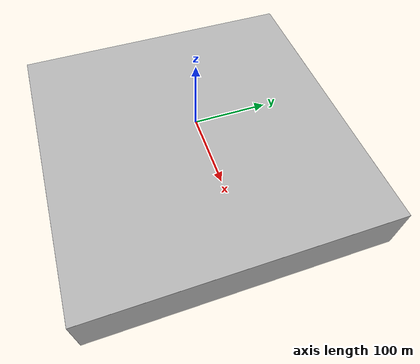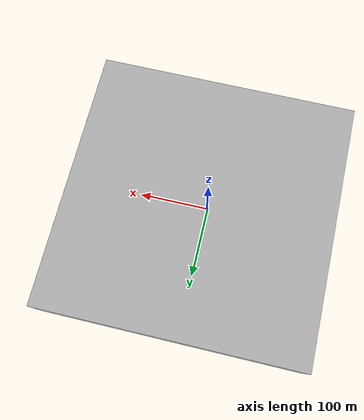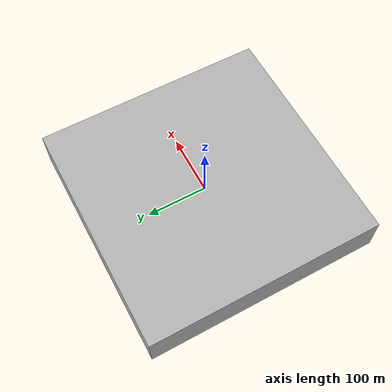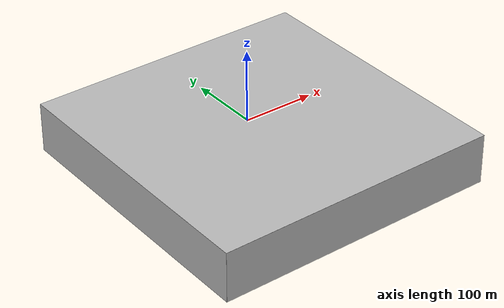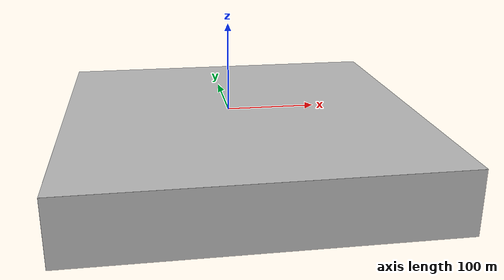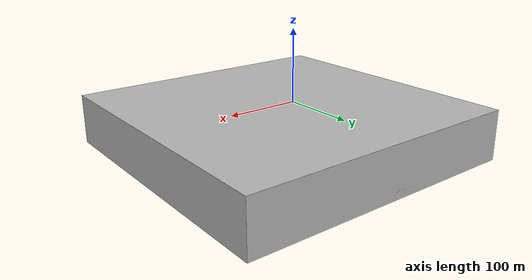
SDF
<sdf version="1.7">
 <world name="munkholmen">
  <physics name="default_physics" default="1" type="ode">
   <max_step_size>0.01</max_step_size>
   <real_time_factor>1</real_time_factor>
   <real_time_update_rate>100</real_time_update_rate>
   <ode>
    <solver>
     <type>quick</type>
     <iters>50</iters>
     <sor>1.2</sor>
     <use_dynamic_moi_rescaling>0</use_dynamic_moi_rescaling>
    </solver>
    <constraints>
     <cfm>0</cfm>
     <erp>0.2</erp>
     <contact_max_correcting_vel>100</contact_max_correcting_vel>
     <contact_surface_layer>0.001</contact_surface_layer>
    </constraints>
   </ode>
  </physics>
  <scene>
   <ambient>0.01 0.01 0.01 1</ambient>
   <sky><clouds><speed>12</speed></clouds></sky>
   <shadows>1</shadows>
   <fog><color>0.1 0.2 0.3 1</color><type>linear</type><density>0.1</density><start>10</start><end>40</end></fog>
   <background>0.7 0.7 0.7 1</background>
  </scene>
  <spherical_coordinates>
   <latitude_deg>63.4534</latitude_deg>
   <longitude_deg>10.4056</longitude_deg>
   <surface_model>EARTH_WGS84</surface_model>
   <elevation>0</elevation>
   <heading_deg>0</heading_deg>
  </spherical_coordinates>
  <light name="sun_diffuse_1" type="directional">
   <pose>-200 -200 100 0 -0 0</pose>
   <diffuse>0.6 0.6 0.6 1</diffuse>
   <specular>0 0 0 1</specular>
   <direction>-0.3 -0.3 -1</direction>
   <attenuation><range>10</range></attenuation>
   <spot><inner_angle>0</inner_angle><outer_angle>0</outer_angle><falloff>0</falloff></spot>
  </light>
  <light name="sun_diffuse_2" type="directional">
   <pose>-100 50 200 0 -0 0</pose>
   <diffuse>0.6 0.6 0.6 1</diffuse>
   <specular>0 0 0 1</specular>
   <direction>-0.3 -0.3 -1</direction>
   <attenuation><range>10</range></attenuation>
   <spot><inner_angle>0</inner_angle><outer_angle>0</outer_angle><falloff>0</falloff></spot>
  </light>
  <light name="sun_diffuse_3" type="directional">
   <pose>-150 -130 50 0 -0 0</pose>
   <diffuse>0.6 0.6 0.6 1</diffuse>
   <specular>0.2 0.2 0.2 1</specular>
   <direction>0.5 0.5 -1</direction>
   <attenuation><range>10</range></attenuation>
   <spot><inner_angle>0</inner_angle><outer_angle>0</outer_angle><falloff>0</falloff></spot>
  </light>
  <model name="herkules_seabed">
   <static>1</static>
   <link name="seabed">
    <collision name="seabed">
     <pose>0 0 -60 0 -0 0</pose>
     <geometry>
      <mesh><uri>model://herkules_seabed/meshes/herkules_seabed.dae</uri><scale>4 4 1</scale></mesh>
     </geometry>
    </collision>
    <visual name="seabed">
     <pose>0 0 -60 0 -0 0</pose>
     <geometry>
      <mesh><uri>model://herkules_seabed/meshes/herkules_seabed.dae</uri><scale>4 4 1</scale></mesh>
     </geometry>
     <material>
      <script>
       <uri>file://Media/materials/scripts/sand.material</uri>
       <name>UUVSimulator/SandAndStones</name>
      </script>
     </material>
    </visual>
   </link>
   <link name="ocean_link">
    <visual name="surface">
     <cast_shadows>0</cast_shadows>
     <geometry><box><size>400 400 0.1</size></box></geometry>
     <material>
      <script><uri>file://Media/materials/scripts/water.material</uri><name>UUVSimulator/StaticWater</name></script>
     </material>
    </visual>
    <visual name="bottom">
     <pose>0 0 -70 0 -0 0</pose>
     <geometry><box><size>400 400 0.1</size></box></geometry>
     <material>
      <script><uri>file://Media/materials/scripts/water.material</uri><name>UUVSimulator/SeaWall</name></script>
     </material>
    </visual>
    <visual name="north_wall">
     <pose>0 200 -35 0 -0 0</pose>
     <geometry><box><size>400 0.1 70</size></box></geometry>
     <material>
      <script><uri>file://Media/materials/scripts/water.material</uri><name>UUVSimulator/SeaWall</name></script>
     </material>
    </visual>
    <visual name="south_wall">
     <pose>0 -200 -35 0 -0 0</pose>
     <geometry><box><size>400 0.1 70</size></box></geometry>
     <material>
      <script><uri>file://Media/materials/scripts/water.material</uri><name>UUVSimulator/SeaWall</name></script>
     </material>
    </visual>
    <visual name="east_wall">
     <pose>200 0 -35 0 -0 0</pose>
     <geometry><box><size>0.1 400 70</size></box></geometry>
     <material>
      <script><uri>file://Media/materials/scripts/water.material</uri><name>UUVSimulator/SeaWall</name></script>
     </material>
    </visual>
    <visual name="west_wall">
     <pose>-200 0 -35 0 -0 0</pose>
     <geometry><box><size>0.1 400 70</size></box></geometry>
     <material>
      <script><uri>file://Media/materials/scripts/water.material</uri><name>UUVSimulator/SeaWall</name></script>
     </material>
    </visual>
   </link>
   <pose>13.2207 -6.8659 0 0 -0 0</pose>
  </model>
  <plugin name="underwater_current_plugin" filename="libuuv_underwater_current_ros_plugin.so">
   <namespace>hydrodynamics</namespace>
   <constant_current>
    <topic>current_velocity</topic>
    <velocity><mean>0</mean><min>0</min><max>5</max><mu>0.0</mu><noiseAmp>0.0</noiseAmp></velocity>
    <horizontal_angle>
     <mean>0</mean>
     <min>-3.141592653589793238</min>
     <max>3.141592653589793238</max>
     <mu>0.0</mu>
     <noiseAmp>0.0</noiseAmp>
    </horizontal_angle>
    <vertical_angle>
     <mean>0</mean>
     <min>-3.141592653589793238</min>
     <max>3.141592653589793238</max>
     <mu>0.0</mu>
     <noiseAmp>0.0</noiseAmp>
    </vertical_angle>
   </constant_current>
  </plugin>
  <plugin name="sc_interface" filename="libuuv_sc_ros_interface_plugin.so"/>
  <gravity>0 0 -9.8</gravity>
  <magnetic_field>6e-06 2.3e-05 -4.2e-05</magnetic_field>
  <atmosphere type="adiabatic"/>
  <model name="person_standing">
   <link name="person_standing::link">
    <inertial>
     <pose>0 -0.1 0.95 0 -0 0</pose>
     <mass>80</mass>
     <inertia><ixx>24.88</ixx><ixy>0</ixy><ixz>0</ixz><iyy>25.73</iyy><iyz>0</iyz><izz>2.48</izz></inertia>
    </inertial>
    <visual name="visual">
     <pose>0 0 0.02 0.04 -0 0</pose>
     <geometry><mesh><uri>model://person_standing/meshes/standing.dae</uri></mesh></geometry>
     <material><shader type="pixel"/></material>
    </visual>
    <collision name="bottom">
     <pose>0 -0.1 0.01 0 -0 0</pose>
     <geometry><box><size>0.5 0.35 0.02</size></box></geometry>
     <surface>
      <friction>
       <ode><mu>1</mu><mu2>1</mu2><fdir1>0 0 0</fdir1><slip1>0</slip1><slip2>0</slip2></ode>
       <torsional>
        <coefficient>1</coefficient>
        <patch_radius>0</patch_radius>
        <surface_radius>0</surface_radius>
        <use_patch_radius>1</use_patch_radius>
        <ode><slip>0</slip></ode>
       </torsional>
      </friction>
      <bounce><restitution_coefficient>0</restitution_coefficient><threshold>1e+06</threshold></bounce>
      <contact>
       <collide_without_contact>0</collide_without_contact>
       <collide_without_contact_bitmask>1</collide_without_contact_bitmask>
       <collide_bitmask>1</collide_bitmask>
       <ode>
        <soft_cfm>0</soft_cfm>
        <soft_erp>0.2</soft_erp>
        <kp>1e+13</kp>
        <kd>1</kd>
        <max_vel>0.01</max_vel>
        <min_depth>0</min_depth>
       </ode>
       <bullet>
        <split_impulse>1</split_impulse>
        <split_impulse_penetration_threshold>-0.01</split_impulse_penetration_threshold>
        <soft_cfm>0</soft_cfm>
        <soft_erp>0.2</soft_erp>
        <kp>1e+13</kp>
        <kd>1</kd>
       </bullet>
      </contact>
     </surface>
    </collision>
    <collision name="person">
     <pose>0 0 0.02 0.04 -0 0</pose>
     <geometry>
      <mesh><uri>/home/vaibhav/.gazebo/models/person_standing/meshes/standing.dae</uri><scale>1 1 1</scale></mesh>
     </geometry>
     <surface>
      <friction>
       <ode><mu>1</mu><mu2>1</mu2><fdir1>0 0 0</fdir1><slip1>0</slip1><slip2>0</slip2></ode>
       <torsional>
        <coefficient>1</coefficient>
        <patch_radius>0</patch_radius>
        <surface_radius>0</surface_radius>
        <use_patch_radius>1</use_patch_radius>
        <ode><slip>0</slip></ode>
       </torsional>
      </friction>
      <bounce><restitution_coefficient>0</restitution_coefficient><threshold>1e+06</threshold></bounce>
      <contact>
       <collide_without_contact>0</collide_without_contact>
       <collide_without_contact_bitmask>1</collide_without_contact_bitmask>
       <collide_bitmask>1</collide_bitmask>
       <ode>
        <soft_cfm>0</soft_cfm>
        <soft_erp>0.2</soft_erp>
        <kp>1e+13</kp>
        <kd>1</kd>
        <max_vel>0.01</max_vel>
        <min_depth>0</min_depth>
       </ode>
       <bullet>
        <split_impulse>1</split_impulse>
        <split_impulse_penetration_threshold>-0.01</split_impulse_penetration_threshold>
        <soft_cfm>0</soft_cfm>
        <soft_erp>0.2</soft_erp>
        <kp>1e+13</kp>
        <kd>1</kd>
       </bullet>
      </contact>
     </surface>
    </collision>
   </link>
   <static>1</static>
   <pose>20 19.9999 -59.8169 -1.57 0 0</pose>
  </model>
  <model name="person_standing_clone">
   <link name="person_standing::link">
    <inertial>
     <pose>0 -0.1 0.95 0 -0 0</pose>
     <mass>80</mass>
     <inertia><ixx>24.88</ixx><ixy>0</ixy><ixz>0</ixz><iyy>25.73</iyy><iyz>0</iyz><izz>2.48</izz></inertia>
    </inertial>
    <visual name="visual">
     <pose>0 0 0.02 0.04 -0 0</pose>
     <geometry><mesh><uri>model://person_standing/meshes/standing.dae</uri></mesh></geometry>
     <material><shader type="pixel"/></material>
    </visual>
    <collision name="bottom">
     <pose>0 -0.1 0.01 0 -0 0</pose>
     <geometry><box><size>0.5 0.35 0.02</size></box></geometry>
     <surface>
      <friction>
       <ode><mu>1</mu><mu2>1</mu2><fdir1>0 0 0</fdir1><slip1>0</slip1><slip2>0</slip2></ode>
       <torsional>
        <coefficient>1</coefficient>
        <patch_radius>0</patch_radius>
        <surface_radius>0</surface_radius>
        <use_patch_radius>1</use_patch_radius>
        <ode><slip>0</slip></ode>
       </torsional>
      </friction>
      <bounce><restitution_coefficient>0</restitution_coefficient><threshold>1e+06</threshold></bounce>
      <contact>
       <collide_without_contact>0</collide_without_contact>
       <collide_without_contact_bitmask>1</collide_without_contact_bitmask>
       <collide_bitmask>1</collide_bitmask>
       <ode>
        <soft_cfm>0</soft_cfm>
        <soft_erp>0.2</soft_erp>
        <kp>1e+13</kp>
        <kd>1</kd>
        <max_vel>0.01</max_vel>
        <min_depth>0</min_depth>
       </ode>
       <bullet>
        <split_impulse>1</split_impulse>
        <split_impulse_penetration_threshold>-0.01</split_impulse_penetration_threshold>
        <soft_cfm>0</soft_cfm>
        <soft_erp>0.2</soft_erp>
        <kp>1e+13</kp>
        <kd>1</kd>
       </bullet>
      </contact>
     </surface>
    </collision>
    <collision name="person">
     <pose>0 0 0.02 0.04 -0 0</pose>
     <geometry>
      <mesh><uri>/home/vaibhav/.gazebo/models/person_standing/meshes/standing.dae</uri><scale>1 1 1</scale></mesh>
     </geometry>
     <surface>
      <friction>
       <ode><mu>1</mu><mu2>1</mu2><fdir1>0 0 0</fdir1><slip1>0</slip1><slip2>0</slip2></ode>
       <torsional>
        <coefficient>1</coefficient>
        <patch_radius>0</patch_radius>
        <surface_radius>0</surface_radius>
        <use_patch_radius>1</use_patch_radius>
        <ode><slip>0</slip></ode>
       </torsional>
      </friction>
      <bounce><restitution_coefficient>0</restitution_coefficient><threshold>1e+06</threshold></bounce>
      <contact>
       <collide_without_contact>0</collide_without_contact>
       <collide_without_contact_bitmask>1</collide_without_contact_bitmask>
       <collide_bitmask>1</collide_bitmask>
       <ode>
        <soft_cfm>0</soft_cfm>
        <soft_erp>0.2</soft_erp>
        <kp>1e+13</kp>
        <kd>1</kd>
        <max_vel>0.01</max_vel>
        <min_depth>0</min_depth>
       </ode>
       <bullet>
        <split_impulse>1</split_impulse>
        <split_impulse_penetration_threshold>-0.01</split_impulse_penetration_threshold>
        <soft_cfm>0</soft_cfm>
        <soft_erp>0.2</soft_erp>
        <kp>1e+13</kp>
        <kd>1</kd>
       </bullet>
      </contact>
     </surface>
    </collision>
   </link>
   <static>1</static>
   <pose>37.4601 2.63761 -59.9 -1.57 0 0</pose>
  </model>
  <model name="person_standing_clone_0">
   <link name="person_standing::link">
    <inertial>
     <pose>0 -0.1 0.95 0 -0 0</pose>
     <mass>80</mass>
     <inertia><ixx>24.88</ixx><ixy>0</ixy><ixz>0</ixz><iyy>25.73</iyy><iyz>0</iyz><izz>2.48</izz></inertia>
    </inertial>
    <visual name="visual">
     <pose>0 0 0.02 0.04 -0 0</pose>
     <geometry><mesh><uri>model://person_standing/meshes/standing.dae</uri></mesh></geometry>
     <material><shader type="pixel"/></material>
    </visual>
    <collision name="bottom">
     <pose>0 -0.1 0.01 0 -0 0</pose>
     <geometry><box><size>0.5 0.35 0.02</size></box></geometry>
     <surface>
      <friction>
       <ode><mu>1</mu><mu2>1</mu2><fdir1>0 0 0</fdir1><slip1>0</slip1><slip2>0</slip2></ode>
       <torsional>
        <coefficient>1</coefficient>
        <patch_radius>0</patch_radius>
        <surface_radius>0</surface_radius>
        <use_patch_radius>1</use_patch_radius>
        <ode><slip>0</slip></ode>
       </torsional>
      </friction>
      <bounce><restitution_coefficient>0</restitution_coefficient><threshold>1e+06</threshold></bounce>
      <contact>
       <collide_without_contact>0</collide_without_contact>
       <collide_without_contact_bitmask>1</collide_without_contact_bitmask>
       <collide_bitmask>1</collide_bitmask>
       <ode>
        <soft_cfm>0</soft_cfm>
        <soft_erp>0.2</soft_erp>
        <kp>1e+13</kp>
        <kd>1</kd>
        <max_vel>0.01</max_vel>
        <min_depth>0</min_depth>
       </ode>
       <bullet>
        <split_impulse>1</split_impulse>
        <split_impulse_penetration_threshold>-0.01</split_impulse_penetration_threshold>
        <soft_cfm>0</soft_cfm>
        <soft_erp>0.2</soft_erp>
        <kp>1e+13</kp>
        <kd>1</kd>
       </bullet>
      </contact>
     </surface>
    </collision>
    <collision name="person">
     <pose>0 0 0.02 0.04 -0 0</pose>
     <geometry>
      <mesh><uri>/home/vaibhav/.gazebo/models/person_standing/meshes/standing.dae</uri><scale>1 1 1</scale></mesh>
     </geometry>
     <surface>
      <friction>
       <ode><mu>1</mu><mu2>1</mu2><fdir1>0 0 0</fdir1><slip1>0</slip1><slip2>0</slip2></ode>
       <torsional>
        <coefficient>1</coefficient>
        <patch_radius>0</patch_radius>
        <surface_radius>0</surface_radius>
        <use_patch_radius>1</use_patch_radius>
        <ode><slip>0</slip></ode>
       </torsional>
      </friction>
      <bounce><restitution_coefficient>0</restitution_coefficient><threshold>1e+06</threshold></bounce>
      <contact>
       <collide_without_contact>0</collide_without_contact>
       <collide_without_contact_bitmask>1</collide_without_contact_bitmask>
       <collide_bitmask>1</collide_bitmask>
       <ode>
        <soft_cfm>0</soft_cfm>
        <soft_erp>0.2</soft_erp>
        <kp>1e+13</kp>
        <kd>1</kd>
        <max_vel>0.01</max_vel>
        <min_depth>0</min_depth>
       </ode>
       <bullet>
        <split_impulse>1</split_impulse>
        <split_impulse_penetration_threshold>-0.01</split_impulse_penetration_threshold>
        <soft_cfm>0</soft_cfm>
        <soft_erp>0.2</soft_erp>
        <kp>1e+13</kp>
        <kd>1</kd>
       </bullet>
      </contact>
     </surface>
    </collision>
   </link>
   <static>1</static>
   <pose>28.0059 -20.863 -59.8 -1.57 0 0</pose>
  </model>
  <model name="person_standing_clone_1">
   <link name="person_standing::link">
    <inertial>
     <pose>0 -0.1 0.95 0 -0 0</pose>
     <mass>80</mass>
     <inertia><ixx>24.88</ixx><ixy>0</ixy><ixz>0</ixz><iyy>25.73</iyy><iyz>0</iyz><izz>2.48</izz></inertia>
    </inertial>
    <visual name="visual">
     <pose>0 0 0.02 0.04 -0 0</pose>
     <geometry><mesh><uri>model://person_standing/meshes/standing.dae</uri></mesh></geometry>
     <material><shader type="pixel"/></material>
    </visual>
    <collision name="bottom">
     <pose>0 -0.1 0.01 0 -0 0</pose>
     <geometry><box><size>0.5 0.35 0.02</size></box></geometry>
     <surface>
      <friction>
       <ode><mu>1</mu><mu2>1</mu2><fdir1>0 0 0</fdir1><slip1>0</slip1><slip2>0</slip2></ode>
       <torsional>
        <coefficient>1</coefficient>
        <patch_radius>0</patch_radius>
        <surface_radius>0</surface_radius>
        <use_patch_radius>1</use_patch_radius>
        <ode><slip>0</slip></ode>
       </torsional>
      </friction>
      <bounce><restitution_coefficient>0</restitution_coefficient><threshold>1e+06</threshold></bounce>
      <contact>
       <collide_without_contact>0</collide_without_contact>
       <collide_without_contact_bitmask>1</collide_without_contact_bitmask>
       <collide_bitmask>1</collide_bitmask>
       <ode>
        <soft_cfm>0</soft_cfm>
        <soft_erp>0.2</soft_erp>
        <kp>1e+13</kp>
        <kd>1</kd>
        <max_vel>0.01</max_vel>
        <min_depth>0</min_depth>
       </ode>
       <bullet>
        <split_impulse>1</split_impulse>
        <split_impulse_penetration_threshold>-0.01</split_impulse_penetration_threshold>
        <soft_cfm>0</soft_cfm>
        <soft_erp>0.2</soft_erp>
        <kp>1e+13</kp>
        <kd>1</kd>
       </bullet>
      </contact>
     </surface>
    </collision>
    <collision name="person">
     <pose>0 0 0.02 0.04 -0 0</pose>
     <geometry>
      <mesh><uri>/home/vaibhav/.gazebo/models/person_standing/meshes/standing.dae</uri><scale>1 1 1</scale></mesh>
     </geometry>
     <surface>
      <friction>
       <ode><mu>1</mu><mu2>1</mu2><fdir1>0 0 0</fdir1><slip1>0</slip1><slip2>0</slip2></ode>
       <torsional>
        <coefficient>1</coefficient>
        <patch_radius>0</patch_radius>
        <surface_radius>0</surface_radius>
        <use_patch_radius>1</use_patch_radius>
        <ode><slip>0</slip></ode>
       </torsional>
      </friction>
      <bounce><restitution_coefficient>0</restitution_coefficient><threshold>1e+06</threshold></bounce>
      <contact>
       <collide_without_contact>0</collide_without_contact>
       <collide_without_contact_bitmask>1</collide_without_contact_bitmask>
       <collide_bitmask>1</collide_bitmask>
       <ode>
        <soft_cfm>0</soft_cfm>
        <soft_erp>0.2</soft_erp>
        <kp>1e+13</kp>
        <kd>1</kd>
        <max_vel>0.01</max_vel>
        <min_depth>0</min_depth>
       </ode>
       <bullet>
        <split_impulse>1</split_impulse>
        <split_impulse_penetration_threshold>-0.01</split_impulse_penetration_threshold>
        <soft_cfm>0</soft_cfm>
        <soft_erp>0.2</soft_erp>
        <kp>1e+13</kp>
        <kd>1</kd>
       </bullet>
      </contact>
     </surface>
    </collision>
   </link>
   <static>1</static>
   <pose>-7.42751 -20.4284 -59.622 -1.57 0 0</pose>
  </model>
  <model name="person_standing_clone_2">
   <link name="person_standing::link">
    <inertial>
     <pose>0 -0.1 0.95 0 -0 0</pose>
     <mass>80</mass>
     <inertia><ixx>24.88</ixx><ixy>0</ixy><ixz>0</ixz><iyy>25.73</iyy><iyz>0</iyz><izz>2.48</izz></inertia>
    </inertial>
    <visual name="visual">
     <pose>0 0 0.02 0.04 -0 0</pose>
     <geometry><mesh><uri>model://person_standing/meshes/standing.dae</uri></mesh></geometry>
     <material><shader type="pixel"/></material>
    </visual>
    <collision name="bottom">
     <pose>0 -0.1 0.01 0 -0 0</pose>
     <geometry><box><size>0.5 0.35 0.02</size></box></geometry>
     <surface>
      <friction>
       <ode><mu>1</mu><mu2>1</mu2><fdir1>0 0 0</fdir1><slip1>0</slip1><slip2>0</slip2></ode>
       <torsional>
        <coefficient>1</coefficient>
        <patch_radius>0</patch_radius>
        <surface_radius>0</surface_radius>
        <use_patch_radius>1</use_patch_radius>
        <ode><slip>0</slip></ode>
       </torsional>
      </friction>
      <bounce><restitution_coefficient>0</restitution_coefficient><threshold>1e+06</threshold></bounce>
      <contact>
       <collide_without_contact>0</collide_without_contact>
       <collide_without_contact_bitmask>1</collide_without_contact_bitmask>
       <collide_bitmask>1</collide_bitmask>
       <ode>
        <soft_cfm>0</soft_cfm>
        <soft_erp>0.2</soft_erp>
        <kp>1e+13</kp>
        <kd>1</kd>
        <max_vel>0.01</max_vel>
        <min_depth>0</min_depth>
       </ode>
       <bullet>
        <split_impulse>1</split_impulse>
        <split_impulse_penetration_threshold>-0.01</split_impulse_penetration_threshold>
        <soft_cfm>0</soft_cfm>
        <soft_erp>0.2</soft_erp>
        <kp>1e+13</kp>
        <kd>1</kd>
       </bullet>
      </contact>
     </surface>
    </collision>
    <collision name="person">
     <pose>0 0 0.02 0.04 -0 0</pose>
     <geometry>
      <mesh><uri>/home/vaibhav/.gazebo/models/person_standing/meshes/standing.dae</uri><scale>1 1 1</scale></mesh>
     </geometry>
     <surface>
      <friction>
       <ode><mu>1</mu><mu2>1</mu2><fdir1>0 0 0</fdir1><slip1>0</slip1><slip2>0</slip2></ode>
       <torsional>
        <coefficient>1</coefficient>
        <patch_radius>0</patch_radius>
        <surface_radius>0</surface_radius>
        <use_patch_radius>1</use_patch_radius>
        <ode><slip>0</slip></ode>
       </torsional>
      </friction>
      <bounce><restitution_coefficient>0</restitution_coefficient><threshold>1e+06</threshold></bounce>
      <contact>
       <collide_without_contact>0</collide_without_contact>
       <collide_without_contact_bitmask>1</collide_without_contact_bitmask>
       <collide_bitmask>1</collide_bitmask>
       <ode>
        <soft_cfm>0</soft_cfm>
        <soft_erp>0.2</soft_erp>
        <kp>1e+13</kp>
        <kd>1</kd>
        <max_vel>0.01</max_vel>
        <min_depth>0</min_depth>
       </ode>
       <bullet>
        <split_impulse>1</split_impulse>
        <split_impulse_penetration_threshold>-0.01</split_impulse_penetration_threshold>
        <soft_cfm>0</soft_cfm>
        <soft_erp>0.2</soft_erp>
        <kp>1e+13</kp>
        <kd>1</kd>
       </bullet>
      </contact>
     </surface>
    </collision>
   </link>
   <static>1</static>
   <pose>2.23624 -18.4416 -59.9496 -1.57 0 0</pose>
  </model>
  <model name="person_standing_clone_3">
   <link name="person_standing::link">
    <inertial>
     <pose>0 -0.1 0.95 0 -0 0</pose>
     <mass>80</mass>
     <inertia><ixx>24.88</ixx><ixy>0</ixy><ixz>0</ixz><iyy>25.73</iyy><iyz>0</iyz><izz>2.48</izz></inertia>
    </inertial>
    <visual name="visual">
     <pose>0 0 0.02 0.04 -0 0</pose>
     <geometry><mesh><uri>model://person_standing/meshes/standing.dae</uri></mesh></geometry>
     <material><shader type="pixel"/></material>
    </visual>
    <collision name="bottom">
     <pose>0 -0.1 0.01 0 -0 0</pose>
     <geometry><box><size>0.5 0.35 0.02</size></box></geometry>
     <surface>
      <friction>
       <ode><mu>1</mu><mu2>1</mu2><fdir1>0 0 0</fdir1><slip1>0</slip1><slip2>0</slip2></ode>
       <torsional>
        <coefficient>1</coefficient>
        <patch_radius>0</patch_radius>
        <surface_radius>0</surface_radius>
        <use_patch_radius>1</use_patch_radius>
        <ode><slip>0</slip></ode>
       </torsional>
      </friction>
      <bounce><restitution_coefficient>0</restitution_coefficient><threshold>1e+06</threshold></bounce>
      <contact>
       <collide_without_contact>0</collide_without_contact>
       <collide_without_contact_bitmask>1</collide_without_contact_bitmask>
       <collide_bitmask>1</collide_bitmask>
       <ode>
        <soft_cfm>0</soft_cfm>
        <soft_erp>0.2</soft_erp>
        <kp>1e+13</kp>
        <kd>1</kd>
        <max_vel>0.01</max_vel>
        <min_depth>0</min_depth>
       </ode>
       <bullet>
        <split_impulse>1</split_impulse>
        <split_impulse_penetration_threshold>-0.01</split_impulse_penetration_threshold>
        <soft_cfm>0</soft_cfm>
        <soft_erp>0.2</soft_erp>
        <kp>1e+13</kp>
        <kd>1</kd>
       </bullet>
      </contact>
     </surface>
    </collision>
    <collision name="person">
     <pose>0 0 0.02 0.04 -0 0</pose>
     <geometry>
      <mesh><uri>/home/vaibhav/.gazebo/models/person_standing/meshes/standing.dae</uri><scale>1 1 1</scale></mesh>
     </geometry>
     <surface>
      <friction>
       <ode><mu>1</mu><mu2>1</mu2><fdir1>0 0 0</fdir1><slip1>0</slip1><slip2>0</slip2></ode>
       <torsional>
        <coefficient>1</coefficient>
        <patch_radius>0</patch_radius>
        <surface_radius>0</surface_radius>
        <use_patch_radius>1</use_patch_radius>
        <ode><slip>0</slip></ode>
       </torsional>
      </friction>
      <bounce><restitution_coefficient>0</restitution_coefficient><threshold>1e+06</threshold></bounce>
      <contact>
       <collide_without_contact>0</collide_without_contact>
       <collide_without_contact_bitmask>1</collide_without_contact_bitmask>
       <collide_bitmask>1</collide_bitmask>
       <ode>
        <soft_cfm>0</soft_cfm>
        <soft_erp>0.2</soft_erp>
        <kp>1e+13</kp>
        <kd>1</kd>
        <max_vel>0.01</max_vel>
        <min_depth>0</min_depth>
       </ode>
       <bullet>
        <split_impulse>1</split_impulse>
        <split_impulse_penetration_threshold>-0.01</split_impulse_penetration_threshold>
        <soft_cfm>0</soft_cfm>
        <soft_erp>0.2</soft_erp>
        <kp>1e+13</kp>
        <kd>1</kd>
       </bullet>
      </contact>
     </surface>
    </collision>
   </link>
   <static>1</static>
   <pose>-10.438 20.6083 -59.6503 -1.57 0 0</pose>
  </model>
  <model name="person_standing_clone_4">
   <link name="person_standing::link">
    <inertial>
     <pose>0 -0.1 0.95 0 -0 0</pose>
     <mass>80</mass>
     <inertia><ixx>24.88</ixx><ixy>0</ixy><ixz>0</ixz><iyy>25.73</iyy><iyz>0</iyz><izz>2.48</izz></inertia>
    </inertial>
    <visual name="visual">
     <pose>0 0 0.02 0.04 -0 0</pose>
     <geometry><mesh><uri>model://person_standing/meshes/standing.dae</uri></mesh></geometry>
     <material><shader type="pixel"/></material>
    </visual>
    <collision name="bottom">
     <pose>0 -0.1 0.01 0 -0 0</pose>
     <geometry><box><size>0.5 0.35 0.02</size></box></geometry>
     <surface>
      <friction>
       <ode><mu>1</mu><mu2>1</mu2><fdir1>0 0 0</fdir1><slip1>0</slip1><slip2>0</slip2></ode>
       <torsional>
        <coefficient>1</coefficient>
        <patch_radius>0</patch_radius>
        <surface_radius>0</surface_radius>
        <use_patch_radius>1</use_patch_radius>
        <ode><slip>0</slip></ode>
       </torsional>
      </friction>
      <bounce><restitution_coefficient>0</restitution_coefficient><threshold>1e+06</threshold></bounce>
      <contact>
       <collide_without_contact>0</collide_without_contact>
       <collide_without_contact_bitmask>1</collide_without_contact_bitmask>
       <collide_bitmask>1</collide_bitmask>
       <ode>
        <soft_cfm>0</soft_cfm>
        <soft_erp>0.2</soft_erp>
        <kp>1e+13</kp>
        <kd>1</kd>
        <max_vel>0.01</max_vel>
        <min_depth>0</min_depth>
       </ode>
       <bullet>
        <split_impulse>1</split_impulse>
        <split_impulse_penetration_threshold>-0.01</split_impulse_penetration_threshold>
        <soft_cfm>0</soft_cfm>
        <soft_erp>0.2</soft_erp>
        <kp>1e+13</kp>
        <kd>1</kd>
       </bullet>
      </contact>
     </surface>
    </collision>
    <collision name="person">
     <pose>0 0 0.02 0.04 -0 0</pose>
     <geometry>
      <mesh><uri>/home/vaibhav/.gazebo/models/person_standing/meshes/standing.dae</uri><scale>1 1 1</scale></mesh>
     </geometry>
     <surface>
      <friction>
       <ode><mu>1</mu><mu2>1</mu2><fdir1>0 0 0</fdir1><slip1>0</slip1><slip2>0</slip2></ode>
       <torsional>
        <coefficient>1</coefficient>
        <patch_radius>0</patch_radius>
        <surface_radius>0</surface_radius>
        <use_patch_radius>1</use_patch_radius>
        <ode><slip>0</slip></ode>
       </torsional>
      </friction>
      <bounce><restitution_coefficient>0</restitution_coefficient><threshold>1e+06</threshold></bounce>
      <contact>
       <collide_without_contact>0</collide_without_contact>
       <collide_without_contact_bitmask>1</collide_without_contact_bitmask>
       <collide_bitmask>1</collide_bitmask>
       <ode>
        <soft_cfm>0</soft_cfm>
        <soft_erp>0.2</soft_erp>
        <kp>1e+13</kp>
        <kd>1</kd>
        <max_vel>0.01</max_vel>
        <min_depth>0</min_depth>
       </ode>
       <bullet>
        <split_impulse>1</split_impulse>
        <split_impulse_penetration_threshold>-0.01</split_impulse_penetration_threshold>
        <soft_cfm>0</soft_cfm>
        <soft_erp>0.2</soft_erp>
        <kp>1e+13</kp>
        <kd>1</kd>
       </bullet>
      </contact>
     </surface>
    </collision>
   </link>
   <static>1</static>
   <pose>-39.1213 -1.32781 -59.691 -1.57 0 0</pose>
  </model>
  <model name="person_standing_clone_5">
   <link name="person_standing::link">
    <inertial>
     <pose>0 -0.1 0.95 0 -0 0</pose>
     <mass>80</mass>
     <inertia><ixx>24.88</ixx><ixy>0</ixy><ixz>0</ixz><iyy>25.73</iyy><iyz>0</iyz><izz>2.48</izz></inertia>
    </inertial>
    <visual name="visual">
     <pose>0 0 0.02 0.04 -0 0</pose>
     <geometry><mesh><uri>model://person_standing/meshes/standing.dae</uri></mesh></geometry>
     <material><shader type="pixel"/></material>
    </visual>
    <collision name="bottom">
     <pose>0 -0.1 0.01 0 -0 0</pose>
     <geometry><box><size>0.5 0.35 0.02</size></box></geometry>
     <surface>
      <friction>
       <ode><mu>1</mu><mu2>1</mu2><fdir1>0 0 0</fdir1><slip1>0</slip1><slip2>0</slip2></ode>
       <torsional>
        <coefficient>1</coefficient>
        <patch_radius>0</patch_radius>
        <surface_radius>0</surface_radius>
        <use_patch_radius>1</use_patch_radius>
        <ode><slip>0</slip></ode>
       </torsional>
      </friction>
      <bounce><restitution_coefficient>0</restitution_coefficient><threshold>1e+06</threshold></bounce>
      <contact>
       <collide_without_contact>0</collide_without_contact>
       <collide_without_contact_bitmask>1</collide_without_contact_bitmask>
       <collide_bitmask>1</collide_bitmask>
       <ode>
        <soft_cfm>0</soft_cfm>
        <soft_erp>0.2</soft_erp>
        <kp>1e+13</kp>
        <kd>1</kd>
        <max_vel>0.01</max_vel>
        <min_depth>0</min_depth>
       </ode>
       <bullet>
        <split_impulse>1</split_impulse>
        <split_impulse_penetration_threshold>-0.01</split_impulse_penetration_threshold>
        <soft_cfm>0</soft_cfm>
        <soft_erp>0.2</soft_erp>
        <kp>1e+13</kp>
        <kd>1</kd>
       </bullet>
      </contact>
     </surface>
    </collision>
    <collision name="person">
     <pose>0 0 0.02 0.04 -0 0</pose>
     <geometry>
      <mesh><uri>/home/vaibhav/.gazebo/models/person_standing/meshes/standing.dae</uri><scale>1 1 1</scale></mesh>
     </geometry>
     <surface>
      <friction>
       <ode><mu>1</mu><mu2>1</mu2><fdir1>0 0 0</fdir1><slip1>0</slip1><slip2>0</slip2></ode>
       <torsional>
        <coefficient>1</coefficient>
        <patch_radius>0</patch_radius>
        <surface_radius>0</surface_radius>
        <use_patch_radius>1</use_patch_radius>
        <ode><slip>0</slip></ode>
       </torsional>
      </friction>
      <bounce><restitution_coefficient>0</restitution_coefficient><threshold>1e+06</threshold></bounce>
      <contact>
       <collide_without_contact>0</collide_without_contact>
       <collide_without_contact_bitmask>1</collide_without_contact_bitmask>
       <collide_bitmask>1</collide_bitmask>
       <ode>
        <soft_cfm>0</soft_cfm>
        <soft_erp>0.2</soft_erp>
        <kp>1e+13</kp>
        <kd>1</kd>
        <max_vel>0.01</max_vel>
        <min_depth>0</min_depth>
       </ode>
       <bullet>
        <split_impulse>1</split_impulse>
        <split_impulse_penetration_threshold>-0.01</split_impulse_penetration_threshold>
        <soft_cfm>0</soft_cfm>
        <soft_erp>0.2</soft_erp>
        <kp>1e+13</kp>
        <kd>1</kd>
       </bullet>
      </contact>
     </surface>
    </collision>
   </link>
   <static>1</static>
   <pose>-31.706 -21.6124 -60 -1.57 0 0</pose>
  </model>
  <model name="person_standing_clone_6">
   <link name="person_standing::link">
    <inertial>
     <pose>0 -0.1 0.95 0 -0 0</pose>
     <mass>80</mass>
     <inertia><ixx>24.88</ixx><ixy>0</ixy><ixz>0</ixz><iyy>25.73</iyy><iyz>0</iyz><izz>2.48</izz></inertia>
    </inertial>
    <visual name="visual">
     <pose>0 0 0.02 0.04 -0 0</pose>
     <geometry><mesh><uri>model://person_standing/meshes/standing.dae</uri></mesh></geometry>
     <material><shader type="pixel"/></material>
    </visual>
    <collision name="bottom">
     <pose>0 -0.1 0.01 0 -0 0</pose>
     <geometry><box><size>0.5 0.35 0.02</size></box></geometry>
     <surface>
      <friction>
       <ode><mu>1</mu><mu2>1</mu2><fdir1>0 0 0</fdir1><slip1>0</slip1><slip2>0</slip2></ode>
       <torsional>
        <coefficient>1</coefficient>
        <patch_radius>0</patch_radius>
        <surface_radius>0</surface_radius>
        <use_patch_radius>1</use_patch_radius>
        <ode><slip>0</slip></ode>
       </torsional>
      </friction>
      <bounce><restitution_coefficient>0</restitution_coefficient><threshold>1e+06</threshold></bounce>
      <contact>
       <collide_without_contact>0</collide_without_contact>
       <collide_without_contact_bitmask>1</collide_without_contact_bitmask>
       <collide_bitmask>1</collide_bitmask>
       <ode>
        <soft_cfm>0</soft_cfm>
        <soft_erp>0.2</soft_erp>
        <kp>1e+13</kp>
        <kd>1</kd>
        <max_vel>0.01</max_vel>
        <min_depth>0</min_depth>
       </ode>
       <bullet>
        <split_impulse>1</split_impulse>
        <split_impulse_penetration_threshold>-0.01</split_impulse_penetration_threshold>
        <soft_cfm>0</soft_cfm>
        <soft_erp>0.2</soft_erp>
        <kp>1e+13</kp>
        <kd>1</kd>
       </bullet>
      </contact>
     </surface>
    </collision>
    <collision name="person">
     <pose>0 0 0.02 0.04 -0 0</pose>
     <geometry>
      <mesh><uri>/home/vaibhav/.gazebo/models/person_standing/meshes/standing.dae</uri><scale>1 1 1</scale></mesh>
     </geometry>
     <surface>
      <friction>
       <ode><mu>1</mu><mu2>1</mu2><fdir1>0 0 0</fdir1><slip1>0</slip1><slip2>0</slip2></ode>
       <torsional>
        <coefficient>1</coefficient>
        <patch_radius>0</patch_radius>
        <surface_radius>0</surface_radius>
        <use_patch_radius>1</use_patch_radius>
        <ode><slip>0</slip></ode>
       </torsional>
      </friction>
      <bounce><restitution_coefficient>0</restitution_coefficient><threshold>1e+06</threshold></bounce>
      <contact>
       <collide_without_contact>0</collide_without_contact>
       <collide_without_contact_bitmask>1</collide_without_contact_bitmask>
       <collide_bitmask>1</collide_bitmask>
       <ode>
        <soft_cfm>0</soft_cfm>
        <soft_erp>0.2</soft_erp>
        <kp>1e+13</kp>
        <kd>1</kd>
        <max_vel>0.01</max_vel>
        <min_depth>0</min_depth>
       </ode>
       <bullet>
        <split_impulse>1</split_impulse>
        <split_impulse_penetration_threshold>-0.01</split_impulse_penetration_threshold>
        <soft_cfm>0</soft_cfm>
        <soft_erp>0.2</soft_erp>
        <kp>1e+13</kp>
        <kd>1</kd>
       </bullet>
      </contact>
     </surface>
    </collision>
   </link>
   <static>1</static>
   <pose>-66.1203 31.3491 -60 -1.57 0 0</pose>
  </model>
  <model name="person_standing_clone_7">
   <link name="person_standing::link">
    <inertial>
     <pose>0 -0.1 0.95 0 -0 0</pose>
     <mass>80</mass>
     <inertia><ixx>24.88</ixx><ixy>0</ixy><ixz>0</ixz><iyy>25.73</iyy><iyz>0</iyz><izz>2.48</izz></inertia>
    </inertial>
    <visual name="visual">
     <pose>0 0 0.02 0.04 -0 0</pose>
     <geometry><mesh><uri>model://person_standing/meshes/standing.dae</uri></mesh></geometry>
     <material><shader type="pixel"/></material>
    </visual>
    <collision name="bottom">
     <pose>0 -0.1 0.01 0 -0 0</pose>
     <geometry><box><size>0.5 0.35 0.02</size></box></geometry>
     <surface>
      <friction>
       <ode><mu>1</mu><mu2>1</mu2><fdir1>0 0 0</fdir1><slip1>0</slip1><slip2>0</slip2></ode>
       <torsional>
        <coefficient>1</coefficient>
        <patch_radius>0</patch_radius>
        <surface_radius>0</surface_radius>
        <use_patch_radius>1</use_patch_radius>
        <ode><slip>0</slip></ode>
       </torsional>
      </friction>
      <bounce><restitution_coefficient>0</restitution_coefficient><threshold>1e+06</threshold></bounce>
      <contact>
       <collide_without_contact>0</collide_without_contact>
       <collide_without_contact_bitmask>1</collide_without_contact_bitmask>
       <collide_bitmask>1</collide_bitmask>
       <ode>
        <soft_cfm>0</soft_cfm>
        <soft_erp>0.2</soft_erp>
        <kp>1e+13</kp>
        <kd>1</kd>
        <max_vel>0.01</max_vel>
        <min_depth>0</min_depth>
       </ode>
       <bullet>
        <split_impulse>1</split_impulse>
        <split_impulse_penetration_threshold>-0.01</split_impulse_penetration_threshold>
        <soft_cfm>0</soft_cfm>
        <soft_erp>0.2</soft_erp>
        <kp>1e+13</kp>
        <kd>1</kd>
       </bullet>
      </contact>
     </surface>
    </collision>
    <collision name="person">
     <pose>0 0 0.02 0.04 -0 0</pose>
     <geometry>
      <mesh><uri>/home/vaibhav/.gazebo/models/person_standing/meshes/standing.dae</uri><scale>1 1 1</scale></mesh>
     </geometry>
     <surface>
      <friction>
       <ode><mu>1</mu><mu2>1</mu2><fdir1>0 0 0</fdir1><slip1>0</slip1><slip2>0</slip2></ode>
       <torsional>
        <coefficient>1</coefficient>
        <patch_radius>0</patch_radius>
        <surface_radius>0</surface_radius>
        <use_patch_radius>1</use_patch_radius>
        <ode><slip>0</slip></ode>
       </torsional>
      </friction>
      <bounce><restitution_coefficient>0</restitution_coefficient><threshold>1e+06</threshold></bounce>
      <contact>
       <collide_without_contact>0</collide_without_contact>
       <collide_without_contact_bitmask>1</collide_without_contact_bitmask>
       <collide_bitmask>1</collide_bitmask>
       <ode>
        <soft_cfm>0</soft_cfm>
        <soft_erp>0.2</soft_erp>
        <kp>1e+13</kp>
        <kd>1</kd>
        <max_vel>0.01</max_vel>
        <min_depth>0</min_depth>
       </ode>
       <bullet>
        <split_impulse>1</split_impulse>
        <split_impulse_penetration_threshold>-0.01</split_impulse_penetration_threshold>
        <soft_cfm>0</soft_cfm>
        <soft_erp>0.2</soft_erp>
        <kp>1e+13</kp>
        <kd>1</kd>
       </bullet>
      </contact>
     </surface>
    </collision>
   </link>
   <static>1</static>
   <pose>-7.3921 53.6339 -59.1119 -1.57 0 0</pose>
  </model>
  <model name="person_standing_clone_8">
   <link name="person_standing::link">
    <inertial>
     <pose>0 -0.1 0.95 0 -0 0</pose>
     <mass>80</mass>
     <inertia><ixx>24.88</ixx><ixy>0</ixy><ixz>0</ixz><iyy>25.73</iyy><iyz>0</iyz><izz>2.48</izz></inertia>
    </inertial>
    <visual name="visual">
     <pose>0 0 0.02 0.04 -0 0</pose>
     <geometry><mesh><uri>model://person_standing/meshes/standing.dae</uri></mesh></geometry>
     <material><shader type="pixel"/></material>
    </visual>
    <collision name="bottom">
     <pose>0 -0.1 0.01 0 -0 0</pose>
     <geometry><box><size>0.5 0.35 0.02</size></box></geometry>
     <surface>
      <friction>
       <ode><mu>1</mu><mu2>1</mu2><fdir1>0 0 0</fdir1><slip1>0</slip1><slip2>0</slip2></ode>
       <torsional>
        <coefficient>1</coefficient>
        <patch_radius>0</patch_radius>
        <surface_radius>0</surface_radius>
        <use_patch_radius>1</use_patch_radius>
        <ode><slip>0</slip></ode>
       </torsional>
      </friction>
      <bounce><restitution_coefficient>0</restitution_coefficient><threshold>1e+06</threshold></bounce>
      <contact>
       <collide_without_contact>0</collide_without_contact>
       <collide_without_contact_bitmask>1</collide_without_contact_bitmask>
       <collide_bitmask>1</collide_bitmask>
       <ode>
        <soft_cfm>0</soft_cfm>
        <soft_erp>0.2</soft_erp>
        <kp>1e+13</kp>
        <kd>1</kd>
        <max_vel>0.01</max_vel>
        <min_depth>0</min_depth>
       </ode>
       <bullet>
        <split_impulse>1</split_impulse>
        <split_impulse_penetration_threshold>-0.01</split_impulse_penetration_threshold>
        <soft_cfm>0</soft_cfm>
        <soft_erp>0.2</soft_erp>
        <kp>1e+13</kp>
        <kd>1</kd>
       </bullet>
      </contact>
     </surface>
    </collision>
    <collision name="person">
     <pose>0 0 0.02 0.04 -0 0</pose>
     <geometry>
      <mesh><uri>/home/vaibhav/.gazebo/models/person_standing/meshes/standing.dae</uri><scale>1 1 1</scale></mesh>
     </geometry>
     <surface>
      <friction>
       <ode><mu>1</mu><mu2>1</mu2><fdir1>0 0 0</fdir1><slip1>0</slip1><slip2>0</slip2></ode>
       <torsional>
        <coefficient>1</coefficient>
        <patch_radius>0</patch_radius>
        <surface_radius>0</surface_radius>
        <use_patch_radius>1</use_patch_radius>
        <ode><slip>0</slip></ode>
       </torsional>
      </friction>
      <bounce><restitution_coefficient>0</restitution_coefficient><threshold>1e+06</threshold></bounce>
      <contact>
       <collide_without_contact>0</collide_without_contact>
       <collide_without_contact_bitmask>1</collide_without_contact_bitmask>
       <collide_bitmask>1</collide_bitmask>
       <ode>
        <soft_cfm>0</soft_cfm>
        <soft_erp>0.2</soft_erp>
        <kp>1e+13</kp>
        <kd>1</kd>
        <max_vel>0.01</max_vel>
        <min_depth>0</min_depth>
       </ode>
       <bullet>
        <split_impulse>1</split_impulse>
        <split_impulse_penetration_threshold>-0.01</split_impulse_penetration_threshold>
        <soft_cfm>0</soft_cfm>
        <soft_erp>0.2</soft_erp>
        <kp>1e+13</kp>
        <kd>1</kd>
       </bullet>
      </contact>
     </surface>
    </collision>
   </link>
   <static>1</static>
   <pose>4.28526 -48.6851 -59.9247 -1.57 0 0</pose>
  </model>
  <model name="person_standing_clone_9">
   <link name="person_standing::link">
    <inertial>
     <pose>0 -0.1 0.95 0 -0 0</pose>
     <mass>80</mass>
     <inertia><ixx>24.88</ixx><ixy>0</ixy><ixz>0</ixz><iyy>25.73</iyy><iyz>0</iyz><izz>2.48</izz></inertia>
    </inertial>
    <visual name="visual">
     <pose>0 0 0.02 0.04 -0 0</pose>
     <geometry><mesh><uri>model://person_standing/meshes/standing.dae</uri></mesh></geometry>
     <material><shader type="pixel"/></material>
    </visual>
    <collision name="bottom">
     <pose>0 -0.1 0.01 0 -0 0</pose>
     <geometry><box><size>0.5 0.35 0.02</size></box></geometry>
     <surface>
      <friction>
       <ode><mu>1</mu><mu2>1</mu2><fdir1>0 0 0</fdir1><slip1>0</slip1><slip2>0</slip2></ode>
       <torsional>
        <coefficient>1</coefficient>
        <patch_radius>0</patch_radius>
        <surface_radius>0</surface_radius>
        <use_patch_radius>1</use_patch_radius>
        <ode><slip>0</slip></ode>
       </torsional>
      </friction>
      <bounce><restitution_coefficient>0</restitution_coefficient><threshold>1e+06</threshold></bounce>
      <contact>
       <collide_without_contact>0</collide_without_contact>
       <collide_without_contact_bitmask>1</collide_without_contact_bitmask>
       <collide_bitmask>1</collide_bitmask>
       <ode>
        <soft_cfm>0</soft_cfm>
        <soft_erp>0.2</soft_erp>
        <kp>1e+13</kp>
        <kd>1</kd>
        <max_vel>0.01</max_vel>
        <min_depth>0</min_depth>
       </ode>
       <bullet>
        <split_impulse>1</split_impulse>
        <split_impulse_penetration_threshold>-0.01</split_impulse_penetration_threshold>
        <soft_cfm>0</soft_cfm>
        <soft_erp>0.2</soft_erp>
        <kp>1e+13</kp>
        <kd>1</kd>
       </bullet>
      </contact>
     </surface>
    </collision>
    <collision name="person">
     <pose>0 0 0.02 0.04 -0 0</pose>
     <geometry>
      <mesh><uri>/home/vaibhav/.gazebo/models/person_standing/meshes/standing.dae</uri><scale>1 1 1</scale></mesh>
     </geometry>
     <surface>
      <friction>
       <ode><mu>1</mu><mu2>1</mu2><fdir1>0 0 0</fdir1><slip1>0</slip1><slip2>0</slip2></ode>
       <torsional>
        <coefficient>1</coefficient>
        <patch_radius>0</patch_radius>
        <surface_radius>0</surface_radius>
        <use_patch_radius>1</use_patch_radius>
        <ode><slip>0</slip></ode>
       </torsional>
      </friction>
      <bounce><restitution_coefficient>0</restitution_coefficient><threshold>1e+06</threshold></bounce>
      <contact>
       <collide_without_contact>0</collide_without_contact>
       <collide_without_contact_bitmask>1</collide_without_contact_bitmask>
       <collide_bitmask>1</collide_bitmask>
       <ode>
        <soft_cfm>0</soft_cfm>
        <soft_erp>0.2</soft_erp>
        <kp>1e+13</kp>
        <kd>1</kd>
        <max_vel>0.01</max_vel>
        <min_depth>0</min_depth>
       </ode>
       <bullet>
        <split_impulse>1</split_impulse>
        <split_impulse_penetration_threshold>-0.01</split_impulse_penetration_threshold>
        <soft_cfm>0</soft_cfm>
        <soft_erp>0.2</soft_erp>
        <kp>1e+13</kp>
        <kd>1</kd>
       </bullet>
      </contact>
     </surface>
    </collision>
   </link>
   <static>1</static>
   <pose>-63.1438 2.93637 -60 -1.57 0 0</pose>
  </model>
  <model name="person_standing_clone_10">
   <link name="person_standing::link">
    <inertial>
     <pose>0 -0.1 0.95 0 -0 0</pose>
     <mass>80</mass>
     <inertia><ixx>24.88</ixx><ixy>0</ixy><ixz>0</ixz><iyy>25.73</iyy><iyz>0</iyz><izz>2.48</izz></inertia>
    </inertial>
    <visual name="visual">
     <pose>0 0 0.02 0.04 -0 0</pose>
     <geometry><mesh><uri>model://person_standing/meshes/standing.dae</uri></mesh></geometry>
     <material><shader type="pixel"/></material>
    </visual>
    <collision name="bottom">
     <pose>0 -0.1 0.01 0 -0 0</pose>
     <geometry><box><size>0.5 0.35 0.02</size></box></geometry>
     <surface>
      <friction>
       <ode><mu>1</mu><mu2>1</mu2><fdir1>0 0 0</fdir1><slip1>0</slip1><slip2>0</slip2></ode>
       <torsional>
        <coefficient>1</coefficient>
        <patch_radius>0</patch_radius>
        <surface_radius>0</surface_radius>
        <use_patch_radius>1</use_patch_radius>
        <ode><slip>0</slip></ode>
       </torsional>
      </friction>
      <bounce><restitution_coefficient>0</restitution_coefficient><threshold>1e+06</threshold></bounce>
      <contact>
       <collide_without_contact>0</collide_without_contact>
       <collide_without_contact_bitmask>1</collide_without_contact_bitmask>
       <collide_bitmask>1</collide_bitmask>
       <ode>
        <soft_cfm>0</soft_cfm>
        <soft_erp>0.2</soft_erp>
        <kp>1e+13</kp>
        <kd>1</kd>
        <max_vel>0.01</max_vel>
        <min_depth>0</min_depth>
       </ode>
       <bullet>
        <split_impulse>1</split_impulse>
        <split_impulse_penetration_threshold>-0.01</split_impulse_penetration_threshold>
        <soft_cfm>0</soft_cfm>
        <soft_erp>0.2</soft_erp>
        <kp>1e+13</kp>
        <kd>1</kd>
       </bullet>
      </contact>
     </surface>
    </collision>
    <collision name="person">
     <pose>0 0 0.02 0.04 -0 0</pose>
     <geometry>
      <mesh><uri>/home/vaibhav/.gazebo/models/person_standing/meshes/standing.dae</uri><scale>1 1 1</scale></mesh>
     </geometry>
     <surface>
      <friction>
       <ode><mu>1</mu><mu2>1</mu2><fdir1>0 0 0</fdir1><slip1>0</slip1><slip2>0</slip2></ode>
       <torsional>
        <coefficient>1</coefficient>
        <patch_radius>0</patch_radius>
        <surface_radius>0</surface_radius>
        <use_patch_radius>1</use_patch_radius>
        <ode><slip>0</slip></ode>
       </torsional>
      </friction>
      <bounce><restitution_coefficient>0</restitution_coefficient><threshold>1e+06</threshold></bounce>
      <contact>
       <collide_without_contact>0</collide_without_contact>
       <collide_without_contact_bitmask>1</collide_without_contact_bitmask>
       <collide_bitmask>1</collide_bitmask>
       <ode>
        <soft_cfm>0</soft_cfm>
        <soft_erp>0.2</soft_erp>
        <kp>1e+13</kp>
        <kd>1</kd>
        <max_vel>0.01</max_vel>
        <min_depth>0</min_depth>
       </ode>
       <bullet>
        <split_impulse>1</split_impulse>
        <split_impulse_penetration_threshold>-0.01</split_impulse_penetration_threshold>
        <soft_cfm>0</soft_cfm>
        <soft_erp>0.2</soft_erp>
        <kp>1e+13</kp>
        <kd>1</kd>
       </bullet>
      </contact>
     </surface>
    </collision>
   </link>
   <static>1</static>
   <pose>-60.3822 -20.1327 -59.6029 -1.57 0 0</pose>
  </model>
  <model name="person_standing_clone_11">
   <link name="person_standing::link">
    <inertial>
     <pose>0 -0.1 0.95 0 -0 0</pose>
     <mass>80</mass>
     <inertia><ixx>24.88</ixx><ixy>0</ixy><ixz>0</ixz><iyy>25.73</iyy><iyz>0</iyz><izz>2.48</izz></inertia>
    </inertial>
    <visual name="visual">
     <pose>0 0 0.02 0.04 -0 0</pose>
     <geometry><mesh><uri>model://person_standing/meshes/standing.dae</uri></mesh></geometry>
     <material><shader type="pixel"/></material>
    </visual>
    <collision name="bottom">
     <pose>0 -0.1 0.01 0 -0 0</pose>
     <geometry><box><size>0.5 0.35 0.02</size></box></geometry>
     <surface>
      <friction>
       <ode><mu>1</mu><mu2>1</mu2><fdir1>0 0 0</fdir1><slip1>0</slip1><slip2>0</slip2></ode>
       <torsional>
        <coefficient>1</coefficient>
        <patch_radius>0</patch_radius>
        <surface_radius>0</surface_radius>
        <use_patch_radius>1</use_patch_radius>
        <ode><slip>0</slip></ode>
       </torsional>
      </friction>
      <bounce><restitution_coefficient>0</restitution_coefficient><threshold>1e+06</threshold></bounce>
      <contact>
       <collide_without_contact>0</collide_without_contact>
       <collide_without_contact_bitmask>1</collide_without_contact_bitmask>
       <collide_bitmask>1</collide_bitmask>
       <ode>
        <soft_cfm>0</soft_cfm>
        <soft_erp>0.2</soft_erp>
        <kp>1e+13</kp>
        <kd>1</kd>
        <max_vel>0.01</max_vel>
        <min_depth>0</min_depth>
       </ode>
       <bullet>
        <split_impulse>1</split_impulse>
        <split_impulse_penetration_threshold>-0.01</split_impulse_penetration_threshold>
        <soft_cfm>0</soft_cfm>
        <soft_erp>0.2</soft_erp>
        <kp>1e+13</kp>
        <kd>1</kd>
       </bullet>
      </contact>
     </surface>
    </collision>
    <collision name="person">
     <pose>0 0 0.02 0.04 -0 0</pose>
     <geometry>
      <mesh><uri>/home/vaibhav/.gazebo/models/person_standing/meshes/standing.dae</uri><scale>1 1 1</scale></mesh>
     </geometry>
     <surface>
      <friction>
       <ode><mu>1</mu><mu2>1</mu2><fdir1>0 0 0</fdir1><slip1>0</slip1><slip2>0</slip2></ode>
       <torsional>
        <coefficient>1</coefficient>
        <patch_radius>0</patch_radius>
        <surface_radius>0</surface_radius>
        <use_patch_radius>1</use_patch_radius>
        <ode><slip>0</slip></ode>
       </torsional>
      </friction>
      <bounce><restitution_coefficient>0</restitution_coefficient><threshold>1e+06</threshold></bounce>
      <contact>
       <collide_without_contact>0</collide_without_contact>
       <collide_without_contact_bitmask>1</collide_without_contact_bitmask>
       <collide_bitmask>1</collide_bitmask>
       <ode>
        <soft_cfm>0</soft_cfm>
        <soft_erp>0.2</soft_erp>
        <kp>1e+13</kp>
        <kd>1</kd>
        <max_vel>0.01</max_vel>
        <min_depth>0</min_depth>
       </ode>
       <bullet>
        <split_impulse>1</split_impulse>
        <split_impulse_penetration_threshold>-0.01</split_impulse_penetration_threshold>
        <soft_cfm>0</soft_cfm>
        <soft_erp>0.2</soft_erp>
        <kp>1e+13</kp>
        <kd>1</kd>
       </bullet>
      </contact>
     </surface>
    </collision>
   </link>
   <static>1</static>
   <pose>-19.2543 -42.3218 -59.7459 -1.57 0 0</pose>
  </model>
  <model name="person_standing_clone_12">
   <link name="person_standing::link">
    <inertial>
     <pose>0 -0.1 0.95 0 -0 0</pose>
     <mass>80</mass>
     <inertia><ixx>24.88</ixx><ixy>0</ixy><ixz>0</ixz><iyy>25.73</iyy><iyz>0</iyz><izz>2.48</izz></inertia>
    </inertial>
    <visual name="visual">
     <pose>0 0 0.02 0.04 -0 0</pose>
     <geometry><mesh><uri>model://person_standing/meshes/standing.dae</uri></mesh></geometry>
     <material><shader type="pixel"/></material>
    </visual>
    <collision name="bottom">
     <pose>0 -0.1 0.01 0 -0 0</pose>
     <geometry><box><size>0.5 0.35 0.02</size></box></geometry>
     <surface>
      <friction>
       <ode><mu>1</mu><mu2>1</mu2><fdir1>0 0 0</fdir1><slip1>0</slip1><slip2>0</slip2></ode>
       <torsional>
        <coefficient>1</coefficient>
        <patch_radius>0</patch_radius>
        <surface_radius>0</surface_radius>
        <use_patch_radius>1</use_patch_radius>
        <ode><slip>0</slip></ode>
       </torsional>
      </friction>
      <bounce><restitution_coefficient>0</restitution_coefficient><threshold>1e+06</threshold></bounce>
      <contact>
       <collide_without_contact>0</collide_without_contact>
       <collide_without_contact_bitmask>1</collide_without_contact_bitmask>
       <collide_bitmask>1</collide_bitmask>
       <ode>
        <soft_cfm>0</soft_cfm>
        <soft_erp>0.2</soft_erp>
        <kp>1e+13</kp>
        <kd>1</kd>
        <max_vel>0.01</max_vel>
        <min_depth>0</min_depth>
       </ode>
       <bullet>
        <split_impulse>1</split_impulse>
        <split_impulse_penetration_threshold>-0.01</split_impulse_penetration_threshold>
        <soft_cfm>0</soft_cfm>
        <soft_erp>0.2</soft_erp>
        <kp>1e+13</kp>
        <kd>1</kd>
       </bullet>
      </contact>
     </surface>
    </collision>
    <collision name="person">
     <pose>0 0 0.02 0.04 -0 0</pose>
     <geometry>
      <mesh><uri>/home/vaibhav/.gazebo/models/person_standing/meshes/standing.dae</uri><scale>1 1 1</scale></mesh>
     </geometry>
     <surface>
      <friction>
       <ode><mu>1</mu><mu2>1</mu2><fdir1>0 0 0</fdir1><slip1>0</slip1><slip2>0</slip2></ode>
       <torsional>
        <coefficient>1</coefficient>
        <patch_radius>0</patch_radius>
        <surface_radius>0</surface_radius>
        <use_patch_radius>1</use_patch_radius>
        <ode><slip>0</slip></ode>
       </torsional>
      </friction>
      <bounce><restitution_coefficient>0</restitution_coefficient><threshold>1e+06</threshold></bounce>
      <contact>
       <collide_without_contact>0</collide_without_contact>
       <collide_without_contact_bitmask>1</collide_without_contact_bitmask>
       <collide_bitmask>1</collide_bitmask>
       <ode>
        <soft_cfm>0</soft_cfm>
        <soft_erp>0.2</soft_erp>
        <kp>1e+13</kp>
        <kd>1</kd>
        <max_vel>0.01</max_vel>
        <min_depth>0</min_depth>
       </ode>
       <bullet>
        <split_impulse>1</split_impulse>
        <split_impulse_penetration_threshold>-0.01</split_impulse_penetration_threshold>
        <soft_cfm>0</soft_cfm>
        <soft_erp>0.2</soft_erp>
        <kp>1e+13</kp>
        <kd>1</kd>
       </bullet>
      </contact>
     </surface>
    </collision>
   </link>
   <static>1</static>
   <pose>29.9577 -48.047 -60 -1.57 0 0</pose>
  </model>
  <model name="person_standing_clone_13">
   <link name="person_standing::link">
    <inertial>
     <pose>0 -0.1 0.95 0 -0 0</pose>
     <mass>80</mass>
     <inertia><ixx>24.88</ixx><ixy>0</ixy><ixz>0</ixz><iyy>25.73</iyy><iyz>0</iyz><izz>2.48</izz></inertia>
    </inertial>
    <visual name="visual">
     <pose>0 0 0.02 0.04 -0 0</pose>
     <geometry><mesh><uri>model://person_standing/meshes/standing.dae</uri></mesh></geometry>
     <material><shader type="pixel"/></material>
    </visual>
    <collision name="bottom">
     <pose>0 -0.1 0.01 0 -0 0</pose>
     <geometry><box><size>0.5 0.35 0.02</size></box></geometry>
     <surface>
      <friction>
       <ode><mu>1</mu><mu2>1</mu2><fdir1>0 0 0</fdir1><slip1>0</slip1><slip2>0</slip2></ode>
       <torsional>
        <coefficient>1</coefficient>
        <patch_radius>0</patch_radius>
        <surface_radius>0</surface_radius>
        <use_patch_radius>1</use_patch_radius>
        <ode><slip>0</slip></ode>
       </torsional>
      </friction>
      <bounce><restitution_coefficient>0</restitution_coefficient><threshold>1e+06</threshold></bounce>
      <contact>
       <collide_without_contact>0</collide_without_contact>
       <collide_without_contact_bitmask>1</collide_without_contact_bitmask>
       <collide_bitmask>1</collide_bitmask>
       <ode>
        <soft_cfm>0</soft_cfm>
        <soft_erp>0.2</soft_erp>
        <kp>1e+13</kp>
        <kd>1</kd>
        <max_vel>0.01</max_vel>
        <min_depth>0</min_depth>
       </ode>
       <bullet>
        <split_impulse>1</split_impulse>
        <split_impulse_penetration_threshold>-0.01</split_impulse_penetration_threshold>
        <soft_cfm>0</soft_cfm>
        <soft_erp>0.2</soft_erp>
        <kp>1e+13</kp>
        <kd>1</kd>
       </bullet>
      </contact>
     </surface>
    </collision>
    <collision name="person">
     <pose>0 0 0.02 0.04 -0 0</pose>
     <geometry>
      <mesh><uri>/home/vaibhav/.gazebo/models/person_standing/meshes/standing.dae</uri><scale>1 1 1</scale></mesh>
     </geometry>
     <surface>
      <friction>
       <ode><mu>1</mu><mu2>1</mu2><fdir1>0 0 0</fdir1><slip1>0</slip1><slip2>0</slip2></ode>
       <torsional>
        <coefficient>1</coefficient>
        <patch_radius>0</patch_radius>
        <surface_radius>0</surface_radius>
        <use_patch_radius>1</use_patch_radius>
        <ode><slip>0</slip></ode>
       </torsional>
      </friction>
      <bounce><restitution_coefficient>0</restitution_coefficient><threshold>1e+06</threshold></bounce>
      <contact>
       <collide_without_contact>0</collide_without_contact>
       <collide_without_contact_bitmask>1</collide_without_contact_bitmask>
       <collide_bitmask>1</collide_bitmask>
       <ode>
        <soft_cfm>0</soft_cfm>
        <soft_erp>0.2</soft_erp>
        <kp>1e+13</kp>
        <kd>1</kd>
        <max_vel>0.01</max_vel>
        <min_depth>0</min_depth>
       </ode>
       <bullet>
        <split_impulse>1</split_impulse>
        <split_impulse_penetration_threshold>-0.01</split_impulse_penetration_threshold>
        <soft_cfm>0</soft_cfm>
        <soft_erp>0.2</soft_erp>
        <kp>1e+13</kp>
        <kd>1</kd>
       </bullet>
      </contact>
     </surface>
    </collision>
   </link>
   <static>1</static>
   <pose>-52.3291 46.7605 -58.9082 -1.57 0 0</pose>
  </model>
  <model name="person_standing_clone_14">
   <link name="person_standing::link">
    <inertial>
     <pose>0 -0.1 0.95 0 -0 0</pose>
     <mass>80</mass>
     <inertia><ixx>24.88</ixx><ixy>0</ixy><ixz>0</ixz><iyy>25.73</iyy><iyz>0</iyz><izz>2.48</izz></inertia>
    </inertial>
    <visual name="visual">
     <pose>0 0 0.02 0.04 -0 0</pose>
     <geometry><mesh><uri>model://person_standing/meshes/standing.dae</uri></mesh></geometry>
     <material><shader type="pixel"/></material>
    </visual>
    <collision name="bottom">
     <pose>0 -0.1 0.01 0 -0 0</pose>
     <geometry><box><size>0.5 0.35 0.02</size></box></geometry>
     <surface>
      <friction>
       <ode><mu>1</mu><mu2>1</mu2><fdir1>0 0 0</fdir1><slip1>0</slip1><slip2>0</slip2></ode>
       <torsional>
        <coefficient>1</coefficient>
        <patch_radius>0</patch_radius>
        <surface_radius>0</surface_radius>
        <use_patch_radius>1</use_patch_radius>
        <ode><slip>0</slip></ode>
       </torsional>
      </friction>
      <bounce><restitution_coefficient>0</restitution_coefficient><threshold>1e+06</threshold></bounce>
      <contact>
       <collide_without_contact>0</collide_without_contact>
       <collide_without_contact_bitmask>1</collide_without_contact_bitmask>
       <collide_bitmask>1</collide_bitmask>
       <ode>
        <soft_cfm>0</soft_cfm>
        <soft_erp>0.2</soft_erp>
        <kp>1e+13</kp>
        <kd>1</kd>
        <max_vel>0.01</max_vel>
        <min_depth>0</min_depth>
       </ode>
       <bullet>
        <split_impulse>1</split_impulse>
        <split_impulse_penetration_threshold>-0.01</split_impulse_penetration_threshold>
        <soft_cfm>0</soft_cfm>
        <soft_erp>0.2</soft_erp>
        <kp>1e+13</kp>
        <kd>1</kd>
       </bullet>
      </contact>
     </surface>
    </collision>
    <collision name="person">
     <pose>0 0 0.02 0.04 -0 0</pose>
     <geometry>
      <mesh><uri>/home/vaibhav/.gazebo/models/person_standing/meshes/standing.dae</uri><scale>1 1 1</scale></mesh>
     </geometry>
     <surface>
      <friction>
       <ode><mu>1</mu><mu2>1</mu2><fdir1>0 0 0</fdir1><slip1>0</slip1><slip2>0</slip2></ode>
       <torsional>
        <coefficient>1</coefficient>
        <patch_radius>0</patch_radius>
        <surface_radius>0</surface_radius>
        <use_patch_radius>1</use_patch_radius>
        <ode><slip>0</slip></ode>
       </torsional>
      </friction>
      <bounce><restitution_coefficient>0</restitution_coefficient><threshold>1e+06</threshold></bounce>
      <contact>
       <collide_without_contact>0</collide_without_contact>
       <collide_without_contact_bitmask>1</collide_without_contact_bitmask>
       <collide_bitmask>1</collide_bitmask>
       <ode>
        <soft_cfm>0</soft_cfm>
        <soft_erp>0.2</soft_erp>
        <kp>1e+13</kp>
        <kd>1</kd>
        <max_vel>0.01</max_vel>
        <min_depth>0</min_depth>
       </ode>
       <bullet>
        <split_impulse>1</split_impulse>
        <split_impulse_penetration_threshold>-0.01</split_impulse_penetration_threshold>
        <soft_cfm>0</soft_cfm>
        <soft_erp>0.2</soft_erp>
        <kp>1e+13</kp>
        <kd>1</kd>
       </bullet>
      </contact>
     </surface>
    </collision>
   </link>
   <static>1</static>
   <pose>-45.445 -51.5425 -59.8038 -1.57 0 0</pose>
  </model>
  <model name="person_standing_clone_15">
   <link name="person_standing::link">
    <inertial>
     <pose>0 -0.1 0.95 0 -0 0</pose>
     <mass>80</mass>
     <inertia><ixx>24.88</ixx><ixy>0</ixy><ixz>0</ixz><iyy>25.73</iyy><iyz>0</iyz><izz>2.48</izz></inertia>
    </inertial>
    <visual name="visual">
     <pose>0 0 0.02 0.04 -0 0</pose>
     <geometry><mesh><uri>model://person_standing/meshes/standing.dae</uri></mesh></geometry>
     <material><shader type="pixel"/></material>
    </visual>
    <collision name="bottom">
     <pose>0 -0.1 0.01 0 -0 0</pose>
     <geometry><box><size>0.5 0.35 0.02</size></box></geometry>
     <surface>
      <friction>
       <ode><mu>1</mu><mu2>1</mu2><fdir1>0 0 0</fdir1><slip1>0</slip1><slip2>0</slip2></ode>
       <torsional>
        <coefficient>1</coefficient>
        <patch_radius>0</patch_radius>
        <surface_radius>0</surface_radius>
        <use_patch_radius>1</use_patch_radius>
        <ode><slip>0</slip></ode>
       </torsional>
      </friction>
      <bounce><restitution_coefficient>0</restitution_coefficient><threshold>1e+06</threshold></bounce>
      <contact>
       <collide_without_contact>0</collide_without_contact>
       <collide_without_contact_bitmask>1</collide_without_contact_bitmask>
       <collide_bitmask>1</collide_bitmask>
       <ode>
        <soft_cfm>0</soft_cfm>
        <soft_erp>0.2</soft_erp>
        <kp>1e+13</kp>
        <kd>1</kd>
        <max_vel>0.01</max_vel>
        <min_depth>0</min_depth>
       </ode>
       <bullet>
        <split_impulse>1</split_impulse>
        <split_impulse_penetration_threshold>-0.01</split_impulse_penetration_threshold>
        <soft_cfm>0</soft_cfm>
        <soft_erp>0.2</soft_erp>
        <kp>1e+13</kp>
        <kd>1</kd>
       </bullet>
      </contact>
     </surface>
    </collision>
    <collision name="person">
     <pose>0 0 0.02 0.04 -0 0</pose>
     <geometry>
      <mesh><uri>/home/vaibhav/.gazebo/models/person_standing/meshes/standing.dae</uri><scale>1 1 1</scale></mesh>
     </geometry>
     <surface>
      <friction>
       <ode><mu>1</mu><mu2>1</mu2><fdir1>0 0 0</fdir1><slip1>0</slip1><slip2>0</slip2></ode>
       <torsional>
        <coefficient>1</coefficient>
        <patch_radius>0</patch_radius>
        <surface_radius>0</surface_radius>
        <use_patch_radius>1</use_patch_radius>
        <ode><slip>0</slip></ode>
       </torsional>
      </friction>
      <bounce><restitution_coefficient>0</restitution_coefficient><threshold>1e+06</threshold></bounce>
      <contact>
       <collide_without_contact>0</collide_without_contact>
       <collide_without_contact_bitmask>1</collide_without_contact_bitmask>
       <collide_bitmask>1</collide_bitmask>
       <ode>
        <soft_cfm>0</soft_cfm>
        <soft_erp>0.2</soft_erp>
        <kp>1e+13</kp>
        <kd>1</kd>
        <max_vel>0.01</max_vel>
        <min_depth>0</min_depth>
       </ode>
       <bullet>
        <split_impulse>1</split_impulse>
        <split_impulse_penetration_threshold>-0.01</split_impulse_penetration_threshold>
        <soft_cfm>0</soft_cfm>
        <soft_erp>0.2</soft_erp>
        <kp>1e+13</kp>
        <kd>1</kd>
       </bullet>
      </contact>
     </surface>
    </collision>
   </link>
   <static>1</static>
   <pose>-17.0146 87.8532 -57.3815 -1.57 0 0</pose>
  </model>
 </world>
</sdf>
